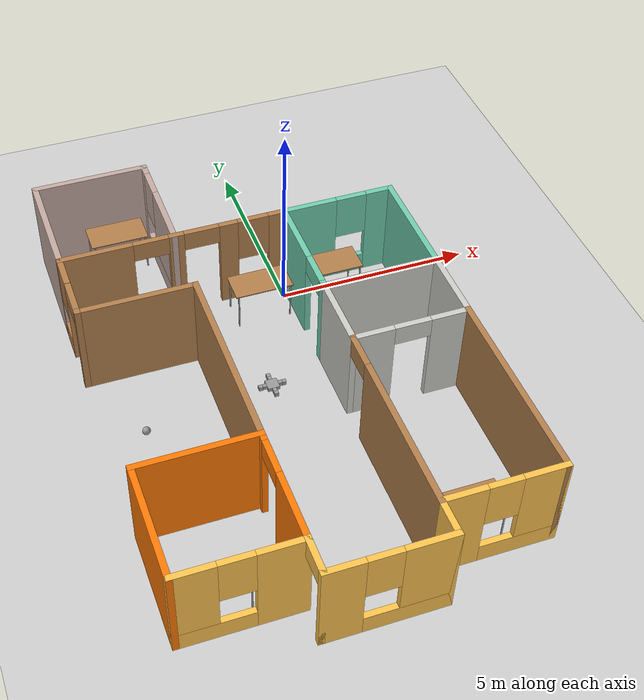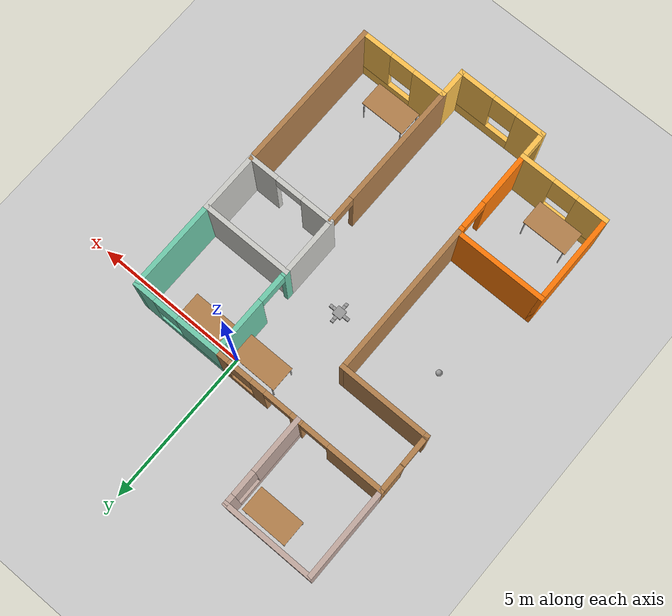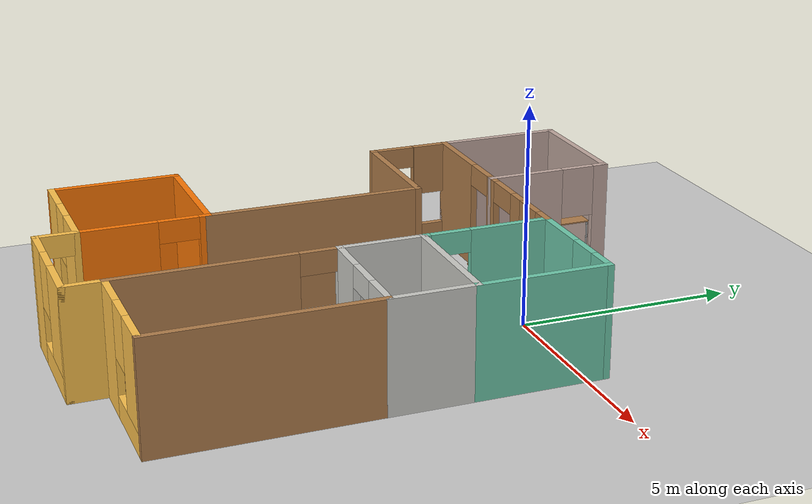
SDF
<sdf version="1.6">
 <world name="default">
  <plugin name="hello" filename="libhello.so"/>
  <light name="sun" type="directional">
   <pose>0 0 10 0 -0 0</pose>
   <diffuse>0.8 0.8 0.8 1</diffuse>
   <specular>0.2 0.2 0.2 1</specular>
   <attenuation>
    <range>1000</range>
    <constant>0.9</constant>
    <linear>0.01</linear>
    <quadratic>0.001</quadratic>
   </attenuation>
   <direction>-0.5 0.1 -0.9</direction>
  </light>
  <model name="ground_plane">
   <static>1</static>
   <link name="link">
    <collision name="collision">
     <geometry><plane><normal>0 0 1</normal><size>100 100</size></plane></geometry>
     <surface>
      <contact><collide_bitmask>65535</collide_bitmask></contact>
      <friction><ode><mu>100</mu><mu2>50</mu2></ode></friction>
     </surface>
    </collision>
    <visual name="visual">
     <cast_shadows>0</cast_shadows>
     <geometry><plane><normal>0 0 1</normal><size>100 100</size></plane></geometry>
     <material>
      <script><uri>file://media/materials/scripts/gazebo.material</uri><name>Gazebo/Grey</name></script>
     </material>
    </visual>
   </link>
  </model>
  <gravity>0 0 -9.8</gravity>
  <magnetic_field>6e-06 2.3e-05 -4.2e-05</magnetic_field>
  <atmosphere type="adiabatic"/>
  <physics name="default_physics" default="0" type="ode">
   <max_step_size>0.001</max_step_size>
   <real_time_factor>1</real_time_factor>
   <real_time_update_rate>1000</real_time_update_rate>
  </physics>
  <scene><ambient>0.4 0.4 0.4 1</ambient><background>0.7 0.7 0.7 1</background><shadows>1</shadows></scene>
  <spherical_coordinates>
   <surface_model>EARTH_WGS84</surface_model>
   <latitude_deg>0</latitude_deg>
   <longitude_deg>0</longitude_deg>
   <elevation>0</elevation>
   <heading_deg>0</heading_deg>
  </spherical_coordinates>
  <model name="myBuilding">
   <pose>-1.28727 -3.3563 0 0 -0 0</pose>
   <link name="Wall_1">
    <pose>0 -6.625 0 0 -0 0</pose>
    <visual name="Wall_1_Visual_0">
     <pose>-1.01471 0 1.25 0 -0 0</pose>
     <geometry><box><size>0.970584 0.15 2.5</size></box></geometry>
     <material>
      <script><uri>file://media/materials/scripts/gazebo.material</uri><name>Gazebo/Grey</name></script>
      <ambient>1 0.764706 0.305882 1</ambient>
     </material>
     <meta><layer>0</layer></meta>
    </visual>
    <collision name="Wall_1_Collision_0">
     <geometry><box><size>0.970584 0.15 2.5</size></box></geometry>
     <pose>-1.01471 0 1.25 0 -0 0</pose>
    </collision>
    <visual name="Wall_1_Visual_1">
     <pose>0.485292 0 0.25 0 -0 0</pose>
     <geometry><box><size>2.02942 0.15 0.5</size></box></geometry>
     <material>
      <script><uri>file://media/materials/scripts/gazebo.material</uri><name>Gazebo/Grey</name></script>
      <ambient>1 0.764706 0.305882 1</ambient>
     </material>
     <meta><layer>0</layer></meta>
    </visual>
    <collision name="Wall_1_Collision_1">
     <geometry><box><size>2.02942 0.15 0.5</size></box></geometry>
     <pose>0.485292 0 0.25 0 -0 0</pose>
    </collision>
    <visual name="Wall_1_Visual_2">
     <pose>0.885292 0 1.5 0 -0 0</pose>
     <geometry><box><size>1.22942 0.15 2</size></box></geometry>
     <material>
      <script><uri>file://media/materials/scripts/gazebo.material</uri><name>Gazebo/Grey</name></script>
      <ambient>1 0.764706 0.305882 1</ambient>
     </material>
     <meta><layer>0</layer></meta>
    </visual>
    <collision name="Wall_1_Collision_2">
     <geometry><box><size>1.22942 0.15 2</size></box></geometry>
     <pose>0.885292 0 1.5 0 -0 0</pose>
    </collision>
    <visual name="Wall_1_Visual_3">
     <pose>-0.129416 0 1.9 0 -0 0</pose>
     <geometry><box><size>0.8 0.15 1.2</size></box></geometry>
     <material>
      <script><uri>file://media/materials/scripts/gazebo.material</uri><name>Gazebo/Grey</name></script>
      <ambient>1 0.764706 0.305882 1</ambient>
     </material>
     <meta><layer>0</layer></meta>
    </visual>
    <collision name="Wall_1_Collision_3">
     <geometry><box><size>0.8 0.15 1.2</size></box></geometry>
     <pose>-0.129416 0 1.9 0 -0 0</pose>
    </collision>
   </link>
   <link name="Wall_10">
    <collision name="Wall_10_Collision">
     <geometry><box><size>3 0.15 2.5</size></box></geometry>
     <pose>0 0 1.25 0 -0 0</pose>
    </collision>
    <visual name="Wall_10_Visual">
     <pose>0 0 1.25 0 -0 0</pose>
     <geometry><box><size>3 0.15 2.5</size></box></geometry>
     <material>
      <script><uri>file://media/materials/scripts/gazebo.material</uri><name>Gazebo/CeilingTiled</name></script>
      <ambient>1 1 1 1</ambient>
     </material>
     <meta><layer>0</layer></meta>
    </visual>
    <pose>2.85 0.925 0 0 -0 3.14159</pose>
   </link>
   <link name="Wall_11">
    <collision name="Wall_11_Collision">
     <geometry><box><size>2 0.15 2.5</size></box></geometry>
     <pose>0 0 1.25 0 -0 0</pose>
    </collision>
    <visual name="Wall_11_Visual">
     <pose>0 0 1.25 0 -0 0</pose>
     <geometry><box><size>2 0.15 2.5</size></box></geometry>
     <material>
      <script><uri>file://media/materials/scripts/gazebo.material</uri><name>Gazebo/CeilingTiled</name></script>
      <ambient>1 1 1 1</ambient>
     </material>
     <meta><layer>0</layer></meta>
    </visual>
    <pose>1.425 0 0 0 0 -1.5708</pose>
   </link>
   <link name="Wall_13">
    <collision name="Wall_13_Collision">
     <geometry><box><size>3 0.15 2.5</size></box></geometry>
     <pose>0 0 1.25 0 -0 0</pose>
    </collision>
    <visual name="Wall_13_Visual">
     <pose>0 0 1.25 0 -0 0</pose>
     <geometry><box><size>3 0.15 2.5</size></box></geometry>
     <material>
      <script><uri>file://media/materials/scripts/gazebo.material</uri><name>Gazebo/Grey</name></script>
      <ambient>0.435294 0.796078 0.67451 1</ambient>
     </material>
     <meta><layer>0</layer></meta>
    </visual>
    <pose>4.275 2.35 0 0 -0 1.5708</pose>
   </link>
   <link name="Wall_14">
    <pose>2.85 3.775 0 0 -0 3.14159</pose>
    <visual name="Wall_14_Visual_0">
     <pose>-1.12972 0 1.25 0 -0 0</pose>
     <geometry><box><size>0.740563 0.15 2.5</size></box></geometry>
     <material>
      <script><uri>file://media/materials/scripts/gazebo.material</uri><name>Gazebo/Grey</name></script>
      <ambient>0.435294 0.796078 0.67451 1</ambient>
     </material>
     <meta><layer>0</layer></meta>
    </visual>
    <collision name="Wall_14_Collision_0">
     <geometry><box><size>0.740563 0.15 2.5</size></box></geometry>
     <pose>-1.12972 0 1.25 0 -0 0</pose>
    </collision>
    <visual name="Wall_14_Visual_1">
     <pose>0.370282 0 0.25 0 -0 0</pose>
     <geometry><box><size>2.25944 0.15 0.5</size></box></geometry>
     <material>
      <script><uri>file://media/materials/scripts/gazebo.material</uri><name>Gazebo/Grey</name></script>
      <ambient>0.435294 0.796078 0.67451 1</ambient>
     </material>
     <meta><layer>0</layer></meta>
    </visual>
    <collision name="Wall_14_Collision_1">
     <geometry><box><size>2.25944 0.15 0.5</size></box></geometry>
     <pose>0.370282 0 0.25 0 -0 0</pose>
    </collision>
    <visual name="Wall_14_Visual_2">
     <pose>0.770282 0 1.5 0 -0 0</pose>
     <geometry><box><size>1.45944 0.15 2</size></box></geometry>
     <material>
      <script><uri>file://media/materials/scripts/gazebo.material</uri><name>Gazebo/Grey</name></script>
      <ambient>0.435294 0.796078 0.67451 1</ambient>
     </material>
     <meta><layer>0</layer></meta>
    </visual>
    <collision name="Wall_14_Collision_2">
     <geometry><box><size>1.45944 0.15 2</size></box></geometry>
     <pose>0.770282 0 1.5 0 -0 0</pose>
    </collision>
    <visual name="Wall_14_Visual_3">
     <pose>-0.359437 0 1.9 0 -0 0</pose>
     <geometry><box><size>0.8 0.15 1.2</size></box></geometry>
     <material>
      <script><uri>file://media/materials/scripts/gazebo.material</uri><name>Gazebo/Grey</name></script>
      <ambient>0.435294 0.796078 0.67451 1</ambient>
     </material>
     <meta><layer>0</layer></meta>
    </visual>
    <collision name="Wall_14_Collision_3">
     <geometry><box><size>0.8 0.15 1.2</size></box></geometry>
     <pose>-0.359437 0 1.9 0 -0 0</pose>
    </collision>
   </link>
   <link name="Wall_15">
    <pose>1.425 2.35 0 0 0 -1.5708</pose>
    <visual name="Wall_15_Visual_0">
     <pose>-0.563237 0 1.25 0 -0 0</pose>
     <geometry><box><size>1.87353 0.15 2.5</size></box></geometry>
     <material>
      <script><uri>file://media/materials/scripts/gazebo.material</uri><name>Gazebo/Grey</name></script>
      <ambient>0.435294 0.796078 0.67451 1</ambient>
     </material>
     <meta><layer>0</layer></meta>
    </visual>
    <collision name="Wall_15_Collision_0">
     <geometry><box><size>1.87353 0.15 2.5</size></box></geometry>
     <pose>-0.563237 0 1.25 0 -0 0</pose>
    </collision>
    <visual name="Wall_15_Visual_1">
     <pose>1.38676 0 1.25 0 -0 0</pose>
     <geometry><box><size>0.226475 0.15 2.5</size></box></geometry>
     <material>
      <script><uri>file://media/materials/scripts/gazebo.material</uri><name>Gazebo/Grey</name></script>
      <ambient>0.435294 0.796078 0.67451 1</ambient>
     </material>
     <meta><layer>0</layer></meta>
    </visual>
    <collision name="Wall_15_Collision_1">
     <geometry><box><size>0.226475 0.15 2.5</size></box></geometry>
     <pose>1.38676 0 1.25 0 -0 0</pose>
    </collision>
    <visual name="Wall_15_Visual_2">
     <pose>0.823525 0 2.25 0 -0 0</pose>
     <geometry><box><size>0.9 0.15 0.5</size></box></geometry>
     <material>
      <script><uri>file://media/materials/scripts/gazebo.material</uri><name>Gazebo/Grey</name></script>
      <ambient>0.435294 0.796078 0.67451 1</ambient>
     </material>
     <meta><layer>0</layer></meta>
    </visual>
    <collision name="Wall_15_Collision_2">
     <geometry><box><size>0.9 0.15 0.5</size></box></geometry>
     <pose>0.823525 0 2.25 0 -0 0</pose>
    </collision>
   </link>
   <link name="Wall_17">
    <pose>-1.425 -6.2 0 0 -0 1.5708</pose>
    <visual name="Wall_17_Visual_0">
     <pose>-0.443398 0 1.25 0 -0 0</pose>
     <geometry><box><size>0.113204 0.15 2.5</size></box></geometry>
     <material>
      <script><uri>file://media/materials/scripts/gazebo.material</uri><name>Gazebo/Grey</name></script>
      <ambient>1 0.764706 0.305882 1</ambient>
     </material>
     <meta><layer>0</layer></meta>
    </visual>
    <collision name="Wall_17_Collision_0">
     <geometry><box><size>0.113204 0.15 2.5</size></box></geometry>
     <pose>-0.443398 0 1.25 0 -0 0</pose>
    </collision>
    <visual name="Wall_17_Visual_1">
     <pose>0.056602 0 2.25 0 -0 0</pose>
     <geometry><box><size>0.886796 0.15 0.5</size></box></geometry>
     <material>
      <script><uri>file://media/materials/scripts/gazebo.material</uri><name>Gazebo/Grey</name></script>
      <ambient>1 0.764706 0.305882 1</ambient>
     </material>
     <meta><layer>0</layer></meta>
    </visual>
    <collision name="Wall_17_Collision_1">
     <geometry><box><size>0.886796 0.15 0.5</size></box></geometry>
     <pose>0.056602 0 2.25 0 -0 0</pose>
    </collision>
   </link>
   <link name="Wall_18">
    <pose>-2.85 -5.775 0 0 -0 3.14159</pose>
    <visual name="Wall_18_Visual_0">
     <pose>-0.922456 0 1.25 0 -0 0</pose>
     <geometry><box><size>1.15509 0.15 2.5</size></box></geometry>
     <material>
      <script><uri>file://media/materials/scripts/gazebo.material</uri><name>Gazebo/Grey</name></script>
      <ambient>1 0.764706 0.305882 1</ambient>
     </material>
     <meta><layer>0</layer></meta>
    </visual>
    <collision name="Wall_18_Collision_0">
     <geometry><box><size>1.15509 0.15 2.5</size></box></geometry>
     <pose>-0.922456 0 1.25 0 -0 0</pose>
    </collision>
    <visual name="Wall_18_Visual_1">
     <pose>0.577544 0 0.25 0 -0 0</pose>
     <geometry><box><size>1.84491 0.15 0.5</size></box></geometry>
     <material>
      <script><uri>file://media/materials/scripts/gazebo.material</uri><name>Gazebo/Grey</name></script>
      <ambient>1 0.764706 0.305882 1</ambient>
     </material>
     <meta><layer>0</layer></meta>
    </visual>
    <collision name="Wall_18_Collision_1">
     <geometry><box><size>1.84491 0.15 0.5</size></box></geometry>
     <pose>0.577544 0 0.25 0 -0 0</pose>
    </collision>
    <visual name="Wall_18_Visual_2">
     <pose>0.977544 0 1.5 0 -0 0</pose>
     <geometry><box><size>1.04491 0.15 2</size></box></geometry>
     <material>
      <script><uri>file://media/materials/scripts/gazebo.material</uri><name>Gazebo/Grey</name></script>
      <ambient>1 0.764706 0.305882 1</ambient>
     </material>
     <meta><layer>0</layer></meta>
    </visual>
    <collision name="Wall_18_Collision_2">
     <geometry><box><size>1.04491 0.15 2</size></box></geometry>
     <pose>0.977544 0 1.5 0 -0 0</pose>
    </collision>
    <visual name="Wall_18_Visual_3">
     <pose>0.055089 0 1.9 0 -0 0</pose>
     <geometry><box><size>0.8 0.15 1.2</size></box></geometry>
     <material>
      <script><uri>file://media/materials/scripts/gazebo.material</uri><name>Gazebo/Grey</name></script>
      <ambient>1 0.764706 0.305882 1</ambient>
     </material>
     <meta><layer>0</layer></meta>
    </visual>
    <collision name="Wall_18_Collision_3">
     <geometry><box><size>0.8 0.15 1.2</size></box></geometry>
     <pose>0.055089 0 1.9 0 -0 0</pose>
    </collision>
   </link>
   <link name="Wall_19">
    <collision name="Wall_19_Collision">
     <geometry><box><size>3 0.15 2.5</size></box></geometry>
     <pose>0 0 1.25 0 -0 0</pose>
    </collision>
    <visual name="Wall_19_Visual">
     <pose>0 0 1.25 0 -0 0</pose>
     <geometry><box><size>3 0.15 2.5</size></box></geometry>
     <material>
      <script><uri>file://media/materials/scripts/gazebo.material</uri><name>Gazebo/Grey</name></script>
      <ambient>0.996078 0.47451 0.0196078 1</ambient>
     </material>
     <meta><layer>0</layer></meta>
    </visual>
    <pose>-4.275 -4.35 0 0 -0 1.5708</pose>
   </link>
   <link name="Wall_2">
    <collision name="Wall_2_Collision">
     <geometry><box><size>1 0.15 2.5</size></box></geometry>
     <pose>0 0 1.25 0 -0 0</pose>
    </collision>
    <visual name="Wall_2_Visual">
     <pose>0 0 1.25 0 -0 0</pose>
     <geometry><box><size>1 0.15 2.5</size></box></geometry>
     <material>
      <script><uri>file://media/materials/scripts/gazebo.material</uri><name>Gazebo/Grey</name></script>
      <ambient>1 0.764706 0.305882 1</ambient>
     </material>
     <meta><layer>0</layer></meta>
    </visual>
    <pose>1.425 -6.2 0 0 -0 1.5708</pose>
   </link>
   <link name="Wall_20">
    <collision name="Wall_20_Collision">
     <geometry><box><size>3 0.15 2.5</size></box></geometry>
     <pose>0 0 1.25 0 -0 0</pose>
    </collision>
    <visual name="Wall_20_Visual">
     <pose>0 0 1.25 0 -0 0</pose>
     <geometry><box><size>3 0.15 2.5</size></box></geometry>
     <material>
      <script><uri>file://media/materials/scripts/gazebo.material</uri><name>Gazebo/Grey</name></script>
      <ambient>0.996078 0.47451 0.0196078 1</ambient>
     </material>
     <meta><layer>0</layer></meta>
    </visual>
    <pose>-2.85 -2.925 0 0 -0 0</pose>
   </link>
   <link name="Wall_21">
    <pose>-1.425 -4.35 0 0 0 -1.5708</pose>
    <visual name="Wall_21_Visual_0">
     <pose>-1.35881 0 1.25 0 -0 0</pose>
     <geometry><box><size>0.282373 0.15 2.5</size></box></geometry>
     <material>
      <script><uri>file://media/materials/scripts/gazebo.material</uri><name>Gazebo/Grey</name></script>
      <ambient>0.996078 0.47451 0.0196078 1</ambient>
     </material>
     <meta><layer>0</layer></meta>
    </visual>
    <collision name="Wall_21_Collision_0">
     <geometry><box><size>0.282373 0.15 2.5</size></box></geometry>
     <pose>-1.35881 0 1.25 0 -0 0</pose>
    </collision>
    <visual name="Wall_21_Visual_1">
     <pose>0.591186 0 1.25 0 -0 0</pose>
     <geometry><box><size>1.81763 0.15 2.5</size></box></geometry>
     <material>
      <script><uri>file://media/materials/scripts/gazebo.material</uri><name>Gazebo/Grey</name></script>
      <ambient>0.996078 0.47451 0.0196078 1</ambient>
     </material>
     <meta><layer>0</layer></meta>
    </visual>
    <collision name="Wall_21_Collision_1">
     <geometry><box><size>1.81763 0.15 2.5</size></box></geometry>
     <pose>0.591186 0 1.25 0 -0 0</pose>
    </collision>
    <visual name="Wall_21_Visual_2">
     <pose>-0.767627 0 2.25 0 -0 0</pose>
     <geometry><box><size>0.9 0.15 0.5</size></box></geometry>
     <material>
      <script><uri>file://media/materials/scripts/gazebo.material</uri><name>Gazebo/Grey</name></script>
      <ambient>0.996078 0.47451 0.0196078 1</ambient>
     </material>
     <meta><layer>0</layer></meta>
    </visual>
    <collision name="Wall_21_Collision_2">
     <geometry><box><size>0.9 0.15 0.5</size></box></geometry>
     <pose>-0.767627 0 2.25 0 -0 0</pose>
    </collision>
   </link>
   <link name="Wall_24">
    <collision name="Wall_24_Collision">
     <geometry><box><size>5 0.15 2.5</size></box></geometry>
     <pose>0 0 1.25 0 -0 0</pose>
    </collision>
    <visual name="Wall_24_Visual">
     <pose>0 0 1.25 0 -0 0</pose>
     <geometry><box><size>5 0.15 2.5</size></box></geometry>
     <material>
      <script><uri>file://media/materials/scripts/gazebo.material</uri><name>Gazebo/Wood</name></script>
      <ambient>1 1 1 1</ambient>
     </material>
     <meta><layer>0</layer></meta>
    </visual>
    <pose>-1.425 -0.5 0 0 -0 1.5708</pose>
   </link>
   <link name="Wall_25">
    <collision name="Wall_25_Collision">
     <geometry><box><size>3 0.15 2.5</size></box></geometry>
     <pose>0 0 1.25 0 -0 0</pose>
    </collision>
    <visual name="Wall_25_Visual">
     <pose>0 0 1.25 0 -0 0</pose>
     <geometry><box><size>3 0.15 2.5</size></box></geometry>
     <material>
      <script><uri>file://media/materials/scripts/gazebo.material</uri><name>Gazebo/Wood</name></script>
      <ambient>1 1 1 1</ambient>
     </material>
     <meta><layer>0</layer></meta>
    </visual>
    <pose>-2.85 1.925 0 0 -0 3.14159</pose>
   </link>
   <link name="Wall_3">
    <pose>2.85 -5.775 0 0 -0 0</pose>
    <visual name="Wall_3_Visual_0">
     <pose>-0.941247 0 1.25 0 -0 0</pose>
     <geometry><box><size>1.11751 0.15 2.5</size></box></geometry>
     <material>
      <script><uri>file://media/materials/scripts/gazebo.material</uri><name>Gazebo/Grey</name></script>
      <ambient>1 0.764706 0.305882 1</ambient>
     </material>
     <meta><layer>0</layer></meta>
    </visual>
    <collision name="Wall_3_Collision_0">
     <geometry><box><size>1.11751 0.15 2.5</size></box></geometry>
     <pose>-0.941247 0 1.25 0 -0 0</pose>
    </collision>
    <visual name="Wall_3_Visual_1">
     <pose>0.558753 0 0.25 0 -0 0</pose>
     <geometry><box><size>1.88249 0.15 0.5</size></box></geometry>
     <material>
      <script><uri>file://media/materials/scripts/gazebo.material</uri><name>Gazebo/Grey</name></script>
      <ambient>1 0.764706 0.305882 1</ambient>
     </material>
     <meta><layer>0</layer></meta>
    </visual>
    <collision name="Wall_3_Collision_1">
     <geometry><box><size>1.88249 0.15 0.5</size></box></geometry>
     <pose>0.558753 0 0.25 0 -0 0</pose>
    </collision>
    <visual name="Wall_3_Visual_2">
     <pose>0.958753 0 1.5 0 -0 0</pose>
     <geometry><box><size>1.08249 0.15 2</size></box></geometry>
     <material>
      <script><uri>file://media/materials/scripts/gazebo.material</uri><name>Gazebo/Grey</name></script>
      <ambient>1 0.764706 0.305882 1</ambient>
     </material>
     <meta><layer>0</layer></meta>
    </visual>
    <collision name="Wall_3_Collision_2">
     <geometry><box><size>1.08249 0.15 2</size></box></geometry>
     <pose>0.958753 0 1.5 0 -0 0</pose>
    </collision>
    <visual name="Wall_3_Visual_3">
     <pose>0.017506 0 1.9 0 -0 0</pose>
     <geometry><box><size>0.8 0.15 1.2</size></box></geometry>
     <material>
      <script><uri>file://media/materials/scripts/gazebo.material</uri><name>Gazebo/Grey</name></script>
      <ambient>1 0.764706 0.305882 1</ambient>
     </material>
     <meta><layer>0</layer></meta>
    </visual>
    <collision name="Wall_3_Collision_3">
     <geometry><box><size>0.8 0.15 1.2</size></box></geometry>
     <pose>0.017506 0 1.9 0 -0 0</pose>
    </collision>
   </link>
   <link name="Wall_30">
    <pose>-4.275 2.85 0 0 -0 1.5708</pose>
    <visual name="Wall_30_Visual_0">
     <pose>-0.914094 0 1.25 0 -0 0</pose>
     <geometry><box><size>0.171813 0.15 2.5</size></box></geometry>
     <material>
      <script><uri>file://media/materials/scripts/gazebo.material</uri><name>Gazebo/Wood</name></script>
      <ambient>1 1 1 1</ambient>
     </material>
     <meta><layer>0</layer></meta>
    </visual>
    <collision name="Wall_30_Collision_0">
     <geometry><box><size>0.171813 0.15 2.5</size></box></geometry>
     <pose>-0.914094 0 1.25 0 -0 0</pose>
    </collision>
    <visual name="Wall_30_Visual_1">
     <pose>0.079254 0 1.25 0 -0 0</pose>
     <geometry><box><size>0.014884 0.15 2.5</size></box></geometry>
     <material>
      <script><uri>file://media/materials/scripts/gazebo.material</uri><name>Gazebo/Wood</name></script>
      <ambient>1 1 1 1</ambient>
     </material>
     <meta><layer>0</layer></meta>
    </visual>
    <collision name="Wall_30_Collision_1">
     <geometry><box><size>0.014884 0.15 2.5</size></box></geometry>
     <pose>0.079254 0 1.25 0 -0 0</pose>
    </collision>
    <visual name="Wall_30_Visual_2">
     <pose>0.543348 0 0.25 0 -0 0</pose>
     <geometry><box><size>0.913304 0.15 0.5</size></box></geometry>
     <material>
      <script><uri>file://media/materials/scripts/gazebo.material</uri><name>Gazebo/Wood</name></script>
      <ambient>1 1 1 1</ambient>
     </material>
     <meta><layer>0</layer></meta>
    </visual>
    <collision name="Wall_30_Collision_2">
     <geometry><box><size>0.913304 0.15 0.5</size></box></geometry>
     <pose>0.543348 0 0.25 0 -0 0</pose>
    </collision>
    <visual name="Wall_30_Visual_3">
     <pose>0.943348 0 1.5 0 -0 0</pose>
     <geometry><box><size>0.113304 0.15 2</size></box></geometry>
     <material>
      <script><uri>file://media/materials/scripts/gazebo.material</uri><name>Gazebo/Wood</name></script>
      <ambient>1 1 1 1</ambient>
     </material>
     <meta><layer>0</layer></meta>
    </visual>
    <collision name="Wall_30_Collision_3">
     <geometry><box><size>0.113304 0.15 2</size></box></geometry>
     <pose>0.943348 0 1.5 0 -0 0</pose>
    </collision>
    <visual name="Wall_30_Visual_4">
     <pose>0.486696 0 1.9 0 -0 0</pose>
     <geometry><box><size>0.8 0.15 1.2</size></box></geometry>
     <material>
      <script><uri>file://media/materials/scripts/gazebo.material</uri><name>Gazebo/Wood</name></script>
      <ambient>1 1 1 1</ambient>
     </material>
     <meta><layer>0</layer></meta>
    </visual>
    <collision name="Wall_30_Collision_4">
     <geometry><box><size>0.8 0.15 1.2</size></box></geometry>
     <pose>0.486696 0 1.9 0 -0 0</pose>
    </collision>
    <visual name="Wall_30_Visual_5">
     <pose>-0.378187 0 2.25 0 -0 0</pose>
     <geometry><box><size>0.9 0.15 0.5</size></box></geometry>
     <material>
      <script><uri>file://media/materials/scripts/gazebo.material</uri><name>Gazebo/Wood</name></script>
      <ambient>1 1 1 1</ambient>
     </material>
     <meta><layer>0</layer></meta>
    </visual>
    <collision name="Wall_30_Collision_5">
     <geometry><box><size>0.9 0.15 0.5</size></box></geometry>
     <pose>-0.378187 0 2.25 0 -0 0</pose>
    </collision>
   </link>
   <link name="Wall_31">
    <pose>-1.425 3.775 0 0 -0 0</pose>
    <visual name="Wall_31_Visual_0">
     <pose>-1.98505 0 1.25 0 -0 0</pose>
     <geometry><box><size>1.87991 0.15 2.5</size></box></geometry>
     <material>
      <script><uri>file://media/materials/scripts/gazebo.material</uri><name>Gazebo/Wood</name></script>
      <ambient>1 1 1 1</ambient>
     </material>
     <meta><layer>0</layer></meta>
    </visual>
    <collision name="Wall_31_Collision_0">
     <geometry><box><size>1.87991 0.15 2.5</size></box></geometry>
     <pose>-1.98505 0 1.25 0 -0 0</pose>
    </collision>
    <visual name="Wall_31_Visual_1">
     <pose>0.048542 0 1.25 0 -0 0</pose>
     <geometry><box><size>0.387269 0.15 2.5</size></box></geometry>
     <material>
      <script><uri>file://media/materials/scripts/gazebo.material</uri><name>Gazebo/Wood</name></script>
      <ambient>1 1 1 1</ambient>
     </material>
     <meta><layer>0</layer></meta>
    </visual>
    <collision name="Wall_31_Collision_1">
     <geometry><box><size>0.387269 0.15 2.5</size></box></geometry>
     <pose>0.048542 0 1.25 0 -0 0</pose>
    </collision>
    <visual name="Wall_31_Visual_2">
     <pose>1.38092 0 1.25 0 -0 0</pose>
     <geometry><box><size>0.477496 0.15 2.5</size></box></geometry>
     <material>
      <script><uri>file://media/materials/scripts/gazebo.material</uri><name>Gazebo/Wood</name></script>
      <ambient>1 1 1 1</ambient>
     </material>
     <meta><layer>0</layer></meta>
    </visual>
    <collision name="Wall_31_Collision_2">
     <geometry><box><size>0.477496 0.15 2.5</size></box></geometry>
     <pose>1.38092 0 1.25 0 -0 0</pose>
    </collision>
    <visual name="Wall_31_Visual_3">
     <pose>2.27234 0 0.25 0 -0 0</pose>
     <geometry><box><size>1.30533 0.15 0.5</size></box></geometry>
     <material>
      <script><uri>file://media/materials/scripts/gazebo.material</uri><name>Gazebo/Wood</name></script>
      <ambient>1 1 1 1</ambient>
     </material>
     <meta><layer>0</layer></meta>
    </visual>
    <collision name="Wall_31_Collision_3">
     <geometry><box><size>1.30533 0.15 0.5</size></box></geometry>
     <pose>2.27234 0 0.25 0 -0 0</pose>
    </collision>
    <visual name="Wall_31_Visual_4">
     <pose>2.67234 0 1.5 0 -0 0</pose>
     <geometry><box><size>0.505327 0.15 2</size></box></geometry>
     <material>
      <script><uri>file://media/materials/scripts/gazebo.material</uri><name>Gazebo/Wood</name></script>
      <ambient>1 1 1 1</ambient>
     </material>
     <meta><layer>0</layer></meta>
    </visual>
    <collision name="Wall_31_Collision_4">
     <geometry><box><size>0.505327 0.15 2</size></box></geometry>
     <pose>2.67234 0 1.5 0 -0 0</pose>
    </collision>
    <visual name="Wall_31_Visual_5">
     <pose>2.01967 0 1.9 0 -0 0</pose>
     <geometry><box><size>0.8 0.15 1.2</size></box></geometry>
     <material>
      <script><uri>file://media/materials/scripts/gazebo.material</uri><name>Gazebo/Wood</name></script>
      <ambient>1 1 1 1</ambient>
     </material>
     <meta><layer>0</layer></meta>
    </visual>
    <collision name="Wall_31_Collision_5">
     <geometry><box><size>0.8 0.15 1.2</size></box></geometry>
     <pose>2.01967 0 1.9 0 -0 0</pose>
    </collision>
    <visual name="Wall_31_Visual_6">
     <pose>-0.595092 0 2.25 0 -0 0</pose>
     <geometry><box><size>0.9 0.15 0.5</size></box></geometry>
     <material>
      <script><uri>file://media/materials/scripts/gazebo.material</uri><name>Gazebo/Wood</name></script>
      <ambient>1 1 1 1</ambient>
     </material>
     <meta><layer>0</layer></meta>
    </visual>
    <collision name="Wall_31_Collision_6">
     <geometry><box><size>0.9 0.15 0.5</size></box></geometry>
     <pose>-0.595092 0 2.25 0 -0 0</pose>
    </collision>
    <visual name="Wall_31_Visual_7">
     <pose>0.692177 0 2.25 0 -0 0</pose>
     <geometry><box><size>0.9 0.15 0.5</size></box></geometry>
     <material>
      <script><uri>file://media/materials/scripts/gazebo.material</uri><name>Gazebo/Wood</name></script>
      <ambient>1 1 1 1</ambient>
     </material>
     <meta><layer>0</layer></meta>
    </visual>
    <collision name="Wall_31_Collision_7">
     <geometry><box><size>0.9 0.15 0.5</size></box></geometry>
     <pose>0.692177 0 2.25 0 -0 0</pose>
    </collision>
   </link>
   <link name="Wall_33">
    <collision name="Wall_33_Collision">
     <geometry><box><size>3 0.15 2.5</size></box></geometry>
     <pose>0 0 1.25 0 -0 0</pose>
    </collision>
    <visual name="Wall_33_Visual">
     <pose>0 0 1.25 0 -0 0</pose>
     <geometry><box><size>3 0.15 2.5</size></box></geometry>
     <material>
      <script><uri>file://media/materials/scripts/gazebo.material</uri><name>Gazebo/Grey</name></script>
      <ambient>0.760784 0.662745 0.627451 1</ambient>
     </material>
     <meta><layer>0</layer></meta>
    </visual>
    <pose>-4.275 5.2 0 0 -0 1.5708</pose>
   </link>
   <link name="Wall_34">
    <collision name="Wall_34_Collision">
     <geometry><box><size>3 0.15 2.5</size></box></geometry>
     <pose>0 0 1.25 0 -0 0</pose>
    </collision>
    <visual name="Wall_34_Visual">
     <pose>0 0 1.25 0 -0 0</pose>
     <geometry><box><size>3 0.15 2.5</size></box></geometry>
     <material>
      <script><uri>file://media/materials/scripts/gazebo.material</uri><name>Gazebo/Grey</name></script>
      <ambient>0.760784 0.662745 0.627451 1</ambient>
     </material>
     <meta><layer>0</layer></meta>
    </visual>
    <pose>-2.85 6.625 0 0 -0 0</pose>
   </link>
   <link name="Wall_35">
    <pose>-1.425 5.2 0 0 0 -1.5708</pose>
    <visual name="Wall_35_Visual_0">
     <pose>-1.31567 0 1.25 0 -0 0</pose>
     <geometry><box><size>0.368653 0.15 2.5</size></box></geometry>
     <material>
      <script><uri>file://media/materials/scripts/gazebo.material</uri><name>Gazebo/Grey</name></script>
      <ambient>0.760784 0.662745 0.627451 1</ambient>
     </material>
     <meta><layer>0</layer></meta>
    </visual>
    <collision name="Wall_35_Collision_0">
     <geometry><box><size>0.368653 0.15 2.5</size></box></geometry>
     <pose>-1.31567 0 1.25 0 -0 0</pose>
    </collision>
    <visual name="Wall_35_Visual_1">
     <pose>0.184327 0 0.25 0 -0 0</pose>
     <geometry><box><size>2.63135 0.15 0.5</size></box></geometry>
     <material>
      <script><uri>file://media/materials/scripts/gazebo.material</uri><name>Gazebo/Grey</name></script>
      <ambient>0.760784 0.662745 0.627451 1</ambient>
     </material>
     <meta><layer>0</layer></meta>
    </visual>
    <collision name="Wall_35_Collision_1">
     <geometry><box><size>2.63135 0.15 0.5</size></box></geometry>
     <pose>0.184327 0 0.25 0 -0 0</pose>
    </collision>
    <visual name="Wall_35_Visual_2">
     <pose>0.584327 0 1.5 0 -0 0</pose>
     <geometry><box><size>1.83135 0.15 2</size></box></geometry>
     <material>
      <script><uri>file://media/materials/scripts/gazebo.material</uri><name>Gazebo/Grey</name></script>
      <ambient>0.760784 0.662745 0.627451 1</ambient>
     </material>
     <meta><layer>0</layer></meta>
    </visual>
    <collision name="Wall_35_Collision_2">
     <geometry><box><size>1.83135 0.15 2</size></box></geometry>
     <pose>0.584327 0 1.5 0 -0 0</pose>
    </collision>
    <visual name="Wall_35_Visual_3">
     <pose>-0.731347 0 1.9 0 -0 0</pose>
     <geometry><box><size>0.8 0.15 1.2</size></box></geometry>
     <material>
      <script><uri>file://media/materials/scripts/gazebo.material</uri><name>Gazebo/Grey</name></script>
      <ambient>0.760784 0.662745 0.627451 1</ambient>
     </material>
     <meta><layer>0</layer></meta>
    </visual>
    <collision name="Wall_35_Collision_3">
     <geometry><box><size>0.8 0.15 1.2</size></box></geometry>
     <pose>-0.731347 0 1.9 0 -0 0</pose>
    </collision>
   </link>
   <link name="Wall_5">
    <collision name="Wall_5_Collision">
     <geometry><box><size>5 0.15 2.5</size></box></geometry>
     <pose>0 0 1.25 0 -0 0</pose>
    </collision>
    <visual name="Wall_5_Visual">
     <pose>0 0 1.25 0 -0 0</pose>
     <geometry><box><size>5 0.15 2.5</size></box></geometry>
     <material>
      <script><uri>file://media/materials/scripts/gazebo.material</uri><name>Gazebo/Wood</name></script>
      <ambient>1 1 1 1</ambient>
     </material>
     <meta><layer>0</layer></meta>
    </visual>
    <pose>4.275 -3.35 0 0 -0 1.5708</pose>
   </link>
   <link name="Wall_6">
    <pose>2.85 -0.925 0 0 -0 3.14159</pose>
    <visual name="Wall_6_Visual_0">
     <pose>-0.99381 0 1.25 0 -0 0</pose>
     <geometry><box><size>1.01238 0.15 2.5</size></box></geometry>
     <material>
      <script><uri>file://media/materials/scripts/gazebo.material</uri><name>Gazebo/CeilingTiled</name></script>
      <ambient>1 1 1 1</ambient>
     </material>
     <meta><layer>0</layer></meta>
    </visual>
    <collision name="Wall_6_Collision_0">
     <geometry><box><size>1.01238 0.15 2.5</size></box></geometry>
     <pose>-0.99381 0 1.25 0 -0 0</pose>
    </collision>
    <visual name="Wall_6_Visual_1">
     <pose>0.95619 0 1.25 0 -0 0</pose>
     <geometry><box><size>1.08762 0.15 2.5</size></box></geometry>
     <material>
      <script><uri>file://media/materials/scripts/gazebo.material</uri><name>Gazebo/CeilingTiled</name></script>
      <ambient>1 1 1 1</ambient>
     </material>
     <meta><layer>0</layer></meta>
    </visual>
    <collision name="Wall_6_Collision_1">
     <geometry><box><size>1.08762 0.15 2.5</size></box></geometry>
     <pose>0.95619 0 1.25 0 -0 0</pose>
    </collision>
    <visual name="Wall_6_Visual_2">
     <pose>-0.03762 0 2.25 0 -0 0</pose>
     <geometry><box><size>0.9 0.15 0.5</size></box></geometry>
     <material>
      <script><uri>file://media/materials/scripts/gazebo.material</uri><name>Gazebo/CeilingTiled</name></script>
      <ambient>1 1 1 1</ambient>
     </material>
     <meta><layer>0</layer></meta>
    </visual>
    <collision name="Wall_6_Collision_2">
     <geometry><box><size>0.9 0.15 0.5</size></box></geometry>
     <pose>-0.03762 0 2.25 0 -0 0</pose>
    </collision>
   </link>
   <link name="Wall_7">
    <pose>1.425 -3.35 0 0 0 -1.5708</pose>
    <visual name="Wall_7_Visual_0">
     <pose>-2.47512 0 1.25 0 -0 0</pose>
     <geometry><box><size>0.049766 0.15 2.5</size></box></geometry>
     <material>
      <script><uri>file://media/materials/scripts/gazebo.material</uri><name>Gazebo/Wood</name></script>
      <ambient>1 1 1 1</ambient>
     </material>
     <meta><layer>0</layer></meta>
    </visual>
    <collision name="Wall_7_Collision_0">
     <geometry><box><size>0.049766 0.15 2.5</size></box></geometry>
     <pose>-2.47512 0 1.25 0 -0 0</pose>
    </collision>
    <visual name="Wall_7_Visual_1">
     <pose>0.474883 0 1.25 0 -0 0</pose>
     <geometry><box><size>4.05023 0.15 2.5</size></box></geometry>
     <material>
      <script><uri>file://media/materials/scripts/gazebo.material</uri><name>Gazebo/Wood</name></script>
      <ambient>1 1 1 1</ambient>
     </material>
     <meta><layer>0</layer></meta>
    </visual>
    <collision name="Wall_7_Collision_1">
     <geometry><box><size>4.05023 0.15 2.5</size></box></geometry>
     <pose>0.474883 0 1.25 0 -0 0</pose>
    </collision>
    <visual name="Wall_7_Visual_2">
     <pose>-2.00023 0 2.25 0 -0 0</pose>
     <geometry><box><size>0.9 0.15 0.5</size></box></geometry>
     <material>
      <script><uri>file://media/materials/scripts/gazebo.material</uri><name>Gazebo/Wood</name></script>
      <ambient>1 1 1 1</ambient>
     </material>
     <meta><layer>0</layer></meta>
    </visual>
    <collision name="Wall_7_Collision_2">
     <geometry><box><size>0.9 0.15 0.5</size></box></geometry>
     <pose>-2.00023 0 2.25 0 -0 0</pose>
    </collision>
   </link>
   <link name="Wall_9">
    <collision name="Wall_9_Collision">
     <geometry><box><size>2 0.15 2.5</size></box></geometry>
     <pose>0 0 1.25 0 -0 0</pose>
    </collision>
    <visual name="Wall_9_Visual">
     <pose>0 0 1.25 0 -0 0</pose>
     <geometry><box><size>2 0.15 2.5</size></box></geometry>
     <material>
      <script><uri>file://media/materials/scripts/gazebo.material</uri><name>Gazebo/CeilingTiled</name></script>
      <ambient>1 1 1 1</ambient>
     </material>
     <meta><layer>0</layer></meta>
    </visual>
    <pose>4.275 0 0 0 -0 1.5708</pose>
   </link>
   <static>1</static>
  </model>
  <model name="myLegged">
   <link name="link_0">
    <pose>0 0 0.044444 0 -0 0</pose>
    <inertial>
     <mass>1</mass>
     <inertia>
      <ixx>0.166667</ixx>
      <ixy>0</ixy>
      <ixz>0</ixz>
      <iyy>0.166667</iyy>
      <iyz>0</iyz>
      <izz>0.166667</izz>
     </inertia>
    </inertial>
    <visual name="visual">
     <geometry><box><size>0.3 0.3 0.1</size></box></geometry>
     <material>
      <lighting>1</lighting>
      <script><uri>file://media/materials/scripts/gazebo.material</uri><name>Gazebo/Grey</name></script>
      <shader type="pixel"><normal_map>__default__</normal_map></shader>
      <ambient>0.3 0.3 0.3 1</ambient>
      <diffuse>0.7 0.7 0.7 1</diffuse>
      <specular>0.01 0.01 0.01 1</specular>
      <emissive>0 0 0 1</emissive>
     </material>
    </visual>
    <collision name="collision">
     <geometry><box><size>0.3 0.3 0.1</size></box></geometry>
     <surface>
      <friction>
       <ode><mu>1</mu><mu2>1</mu2><fdir1>0 0 0</fdir1><slip1>0</slip1><slip2>0</slip2></ode>
       <torsional>
        <coefficient>1</coefficient>
        <patch_radius>0</patch_radius>
        <surface_radius>0</surface_radius>
        <use_patch_radius>1</use_patch_radius>
        <ode><slip>0</slip></ode>
       </torsional>
      </friction>
      <bounce><restitution_coefficient>0</restitution_coefficient><threshold>1e+06</threshold></bounce>
      <contact>
       <collide_without_contact>0</collide_without_contact>
       <collide_without_contact_bitmask>1</collide_without_contact_bitmask>
       <collide_bitmask>1</collide_bitmask>
       <ode>
        <soft_cfm>0</soft_cfm>
        <soft_erp>0.2</soft_erp>
        <kp>1e+13</kp>
        <kd>1</kd>
        <max_vel>0.01</max_vel>
        <min_depth>0</min_depth>
       </ode>
       <bullet>
        <split_impulse>1</split_impulse>
        <split_impulse_penetration_threshold>-0.01</split_impulse_penetration_threshold>
        <soft_cfm>0</soft_cfm>
        <soft_erp>0.2</soft_erp>
        <kp>1e+13</kp>
        <kd>1</kd>
       </bullet>
      </contact>
     </surface>
    </collision>
   </link>
   <link name="link_1">
    <pose>0 -0.2 0.044444 0 -0 0</pose>
    <inertial>
     <mass>1</mass>
     <inertia>
      <ixx>0.166667</ixx>
      <ixy>0</ixy>
      <ixz>0</ixz>
      <iyy>0.166667</iyy>
      <iyz>0</iyz>
      <izz>0.166667</izz>
     </inertia>
    </inertial>
    <visual name="visual">
     <geometry><box><size>0.1 0.1 0.1</size></box></geometry>
     <material>
      <lighting>1</lighting>
      <script><uri>file://media/materials/scripts/gazebo.material</uri><name>Gazebo/Grey</name></script>
      <shader type="pixel"><normal_map>__default__</normal_map></shader>
      <ambient>0.3 0.3 0.3 1</ambient>
      <diffuse>0.7 0.7 0.7 1</diffuse>
      <specular>0.01 0.01 0.01 1</specular>
      <emissive>0 0 0 1</emissive>
     </material>
    </visual>
    <collision name="collision">
     <geometry><box><size>0.1 0.1 0.1</size></box></geometry>
     <surface>
      <friction>
       <ode><mu>1</mu><mu2>1</mu2><fdir1>0 0 0</fdir1><slip1>0</slip1><slip2>0</slip2></ode>
       <torsional>
        <coefficient>1</coefficient>
        <patch_radius>0</patch_radius>
        <surface_radius>0</surface_radius>
        <use_patch_radius>1</use_patch_radius>
        <ode><slip>0</slip></ode>
       </torsional>
      </friction>
      <bounce><restitution_coefficient>0</restitution_coefficient><threshold>1e+06</threshold></bounce>
      <contact>
       <collide_without_contact>0</collide_without_contact>
       <collide_without_contact_bitmask>1</collide_without_contact_bitmask>
       <collide_bitmask>1</collide_bitmask>
       <ode>
        <soft_cfm>0</soft_cfm>
        <soft_erp>0.2</soft_erp>
        <kp>1e+13</kp>
        <kd>1</kd>
        <max_vel>0.01</max_vel>
        <min_depth>0</min_depth>
       </ode>
       <bullet>
        <split_impulse>1</split_impulse>
        <split_impulse_penetration_threshold>-0.01</split_impulse_penetration_threshold>
        <soft_cfm>0</soft_cfm>
        <soft_erp>0.2</soft_erp>
        <kp>1e+13</kp>
        <kd>1</kd>
       </bullet>
      </contact>
     </surface>
    </collision>
   </link>
   <link name="link_1_clone">
    <pose>-0.2 0 0.044444 0 -0 0</pose>
    <inertial>
     <mass>1</mass>
     <inertia>
      <ixx>0.166667</ixx>
      <ixy>0</ixy>
      <ixz>0</ixz>
      <iyy>0.166667</iyy>
      <iyz>0</iyz>
      <izz>0.166667</izz>
     </inertia>
    </inertial>
    <visual name="visual">
     <geometry><box><size>0.1 0.1 0.1</size></box></geometry>
     <material>
      <lighting>1</lighting>
      <script><uri>file://media/materials/scripts/gazebo.material</uri><name>Gazebo/Grey</name></script>
      <shader type="pixel"><normal_map>__default__</normal_map></shader>
      <ambient>0.3 0.3 0.3 1</ambient>
      <diffuse>0.7 0.7 0.7 1</diffuse>
      <specular>0.01 0.01 0.01 1</specular>
      <emissive>0 0 0 1</emissive>
     </material>
    </visual>
    <collision name="collision">
     <geometry><box><size>0.1 0.1 0.1</size></box></geometry>
     <surface>
      <friction>
       <ode><mu>1</mu><mu2>1</mu2><fdir1>0 0 0</fdir1><slip1>0</slip1><slip2>0</slip2></ode>
       <torsional>
        <coefficient>1</coefficient>
        <patch_radius>0</patch_radius>
        <surface_radius>0</surface_radius>
        <use_patch_radius>1</use_patch_radius>
        <ode><slip>0</slip></ode>
       </torsional>
      </friction>
      <bounce><restitution_coefficient>0</restitution_coefficient><threshold>1e+06</threshold></bounce>
      <contact>
       <collide_without_contact>0</collide_without_contact>
       <collide_without_contact_bitmask>1</collide_without_contact_bitmask>
       <collide_bitmask>1</collide_bitmask>
       <ode>
        <soft_cfm>0</soft_cfm>
        <soft_erp>0.2</soft_erp>
        <kp>1e+13</kp>
        <kd>1</kd>
        <max_vel>0.01</max_vel>
        <min_depth>0</min_depth>
       </ode>
       <bullet>
        <split_impulse>1</split_impulse>
        <split_impulse_penetration_threshold>-0.01</split_impulse_penetration_threshold>
        <soft_cfm>0</soft_cfm>
        <soft_erp>0.2</soft_erp>
        <kp>1e+13</kp>
        <kd>1</kd>
       </bullet>
      </contact>
     </surface>
    </collision>
   </link>
   <link name="link_1_clone_0">
    <pose>0.2 0 0.044444 0 -0 0</pose>
    <inertial>
     <mass>1</mass>
     <inertia>
      <ixx>0.166667</ixx>
      <ixy>0</ixy>
      <ixz>0</ixz>
      <iyy>0.166667</iyy>
      <iyz>0</iyz>
      <izz>0.166667</izz>
     </inertia>
    </inertial>
    <visual name="visual">
     <geometry><box><size>0.1 0.1 0.1</size></box></geometry>
     <material>
      <lighting>1</lighting>
      <script><uri>file://media/materials/scripts/gazebo.material</uri><name>Gazebo/Grey</name></script>
      <shader type="pixel"><normal_map>__default__</normal_map></shader>
      <ambient>0.3 0.3 0.3 1</ambient>
      <diffuse>0.7 0.7 0.7 1</diffuse>
      <specular>0.01 0.01 0.01 1</specular>
      <emissive>0 0 0 1</emissive>
     </material>
    </visual>
    <collision name="collision">
     <geometry><box><size>0.1 0.1 0.1</size></box></geometry>
     <surface>
      <friction>
       <ode><mu>1</mu><mu2>1</mu2><fdir1>0 0 0</fdir1><slip1>0</slip1><slip2>0</slip2></ode>
       <torsional>
        <coefficient>1</coefficient>
        <patch_radius>0</patch_radius>
        <surface_radius>0</surface_radius>
        <use_patch_radius>1</use_patch_radius>
        <ode><slip>0</slip></ode>
       </torsional>
      </friction>
      <bounce><restitution_coefficient>0</restitution_coefficient><threshold>1e+06</threshold></bounce>
      <contact>
       <collide_without_contact>0</collide_without_contact>
       <collide_without_contact_bitmask>1</collide_without_contact_bitmask>
       <collide_bitmask>1</collide_bitmask>
       <ode>
        <soft_cfm>0</soft_cfm>
        <soft_erp>0.2</soft_erp>
        <kp>1e+13</kp>
        <kd>1</kd>
        <max_vel>0.01</max_vel>
        <min_depth>0</min_depth>
       </ode>
       <bullet>
        <split_impulse>1</split_impulse>
        <split_impulse_penetration_threshold>-0.01</split_impulse_penetration_threshold>
        <soft_cfm>0</soft_cfm>
        <soft_erp>0.2</soft_erp>
        <kp>1e+13</kp>
        <kd>1</kd>
       </bullet>
      </contact>
     </surface>
    </collision>
   </link>
   <link name="link_1_clone_1">
    <pose>0 0.2 0.044444 0 -0 0</pose>
    <inertial>
     <mass>1</mass>
     <inertia>
      <ixx>0.166667</ixx>
      <ixy>0</ixy>
      <ixz>0</ixz>
      <iyy>0.166667</iyy>
      <iyz>0</iyz>
      <izz>0.166667</izz>
     </inertia>
    </inertial>
    <visual name="visual">
     <geometry><box><size>0.1 0.1 0.1</size></box></geometry>
     <material>
      <lighting>1</lighting>
      <script><uri>file://media/materials/scripts/gazebo.material</uri><name>Gazebo/Grey</name></script>
      <shader type="pixel"><normal_map>__default__</normal_map></shader>
      <ambient>0.3 0.3 0.3 1</ambient>
      <diffuse>0.7 0.7 0.7 1</diffuse>
      <specular>0.01 0.01 0.01 1</specular>
      <emissive>0 0 0 1</emissive>
     </material>
    </visual>
    <collision name="collision">
     <geometry><box><size>0.1 0.1 0.1</size></box></geometry>
     <surface>
      <friction>
       <ode><mu>1</mu><mu2>1</mu2><fdir1>0 0 0</fdir1><slip1>0</slip1><slip2>0</slip2></ode>
       <torsional>
        <coefficient>1</coefficient>
        <patch_radius>0</patch_radius>
        <surface_radius>0</surface_radius>
        <use_patch_radius>1</use_patch_radius>
        <ode><slip>0</slip></ode>
       </torsional>
      </friction>
      <bounce><restitution_coefficient>0</restitution_coefficient><threshold>1e+06</threshold></bounce>
      <contact>
       <collide_without_contact>0</collide_without_contact>
       <collide_without_contact_bitmask>1</collide_without_contact_bitmask>
       <collide_bitmask>1</collide_bitmask>
       <ode>
        <soft_cfm>0</soft_cfm>
        <soft_erp>0.2</soft_erp>
        <kp>1e+13</kp>
        <kd>1</kd>
        <max_vel>0.01</max_vel>
        <min_depth>0</min_depth>
       </ode>
       <bullet>
        <split_impulse>1</split_impulse>
        <split_impulse_penetration_threshold>-0.01</split_impulse_penetration_threshold>
        <soft_cfm>0</soft_cfm>
        <soft_erp>0.2</soft_erp>
        <kp>1e+13</kp>
        <kd>1</kd>
       </bullet>
      </contact>
     </surface>
    </collision>
   </link>
   <link name="link_2">
    <pose>0 -0.3 -0.055556 0 -0 0</pose>
    <inertial>
     <mass>1</mass>
     <inertia>
      <ixx>0.166667</ixx>
      <ixy>0</ixy>
      <ixz>0</ixz>
      <iyy>0.166667</iyy>
      <iyz>0</iyz>
      <izz>0.166667</izz>
     </inertia>
    </inertial>
    <visual name="visual">
     <geometry><box><size>0.1 0.1 0.3</size></box></geometry>
     <material>
      <lighting>1</lighting>
      <script><uri>file://media/materials/scripts/gazebo.material</uri><name>Gazebo/Grey</name></script>
      <shader type="pixel"><normal_map>__default__</normal_map></shader>
      <ambient>0.3 0.3 0.3 1</ambient>
      <diffuse>0.7 0.7 0.7 1</diffuse>
      <specular>0.01 0.01 0.01 1</specular>
      <emissive>0 0 0 1</emissive>
     </material>
    </visual>
    <collision name="collision">
     <geometry><box><size>0.1 0.1 0.3</size></box></geometry>
     <surface>
      <friction>
       <ode><mu>1</mu><mu2>1</mu2><fdir1>0 0 0</fdir1><slip1>0</slip1><slip2>0</slip2></ode>
       <torsional>
        <coefficient>1</coefficient>
        <patch_radius>0</patch_radius>
        <surface_radius>0</surface_radius>
        <use_patch_radius>1</use_patch_radius>
        <ode><slip>0</slip></ode>
       </torsional>
      </friction>
      <bounce><restitution_coefficient>0</restitution_coefficient><threshold>1e+06</threshold></bounce>
      <contact>
       <collide_without_contact>0</collide_without_contact>
       <collide_without_contact_bitmask>1</collide_without_contact_bitmask>
       <collide_bitmask>1</collide_bitmask>
       <ode>
        <soft_cfm>0</soft_cfm>
        <soft_erp>0.2</soft_erp>
        <kp>1e+13</kp>
        <kd>1</kd>
        <max_vel>0.01</max_vel>
        <min_depth>0</min_depth>
       </ode>
       <bullet>
        <split_impulse>1</split_impulse>
        <split_impulse_penetration_threshold>-0.01</split_impulse_penetration_threshold>
        <soft_cfm>0</soft_cfm>
        <soft_erp>0.2</soft_erp>
        <kp>1e+13</kp>
        <kd>1</kd>
       </bullet>
      </contact>
     </surface>
    </collision>
   </link>
   <link name="link_2_clone">
    <pose>-0.3 0 -0.055556 0 -0 0</pose>
    <inertial>
     <mass>1</mass>
     <inertia>
      <ixx>0.166667</ixx>
      <ixy>0</ixy>
      <ixz>0</ixz>
      <iyy>0.166667</iyy>
      <iyz>0</iyz>
      <izz>0.166667</izz>
     </inertia>
    </inertial>
    <visual name="visual">
     <geometry><box><size>0.1 0.1 0.3</size></box></geometry>
     <material>
      <lighting>1</lighting>
      <script><uri>file://media/materials/scripts/gazebo.material</uri><name>Gazebo/Grey</name></script>
      <shader type="pixel"><normal_map>__default__</normal_map></shader>
      <ambient>0.3 0.3 0.3 1</ambient>
      <diffuse>0.7 0.7 0.7 1</diffuse>
      <specular>0.01 0.01 0.01 1</specular>
      <emissive>0 0 0 1</emissive>
     </material>
    </visual>
    <collision name="collision">
     <geometry><box><size>0.1 0.1 0.3</size></box></geometry>
     <surface>
      <friction>
       <ode><mu>1</mu><mu2>1</mu2><fdir1>0 0 0</fdir1><slip1>0</slip1><slip2>0</slip2></ode>
       <torsional>
        <coefficient>1</coefficient>
        <patch_radius>0</patch_radius>
        <surface_radius>0</surface_radius>
        <use_patch_radius>1</use_patch_radius>
        <ode><slip>0</slip></ode>
       </torsional>
      </friction>
      <bounce><restitution_coefficient>0</restitution_coefficient><threshold>1e+06</threshold></bounce>
      <contact>
       <collide_without_contact>0</collide_without_contact>
       <collide_without_contact_bitmask>1</collide_without_contact_bitmask>
       <collide_bitmask>1</collide_bitmask>
       <ode>
        <soft_cfm>0</soft_cfm>
        <soft_erp>0.2</soft_erp>
        <kp>1e+13</kp>
        <kd>1</kd>
        <max_vel>0.01</max_vel>
        <min_depth>0</min_depth>
       </ode>
       <bullet>
        <split_impulse>1</split_impulse>
        <split_impulse_penetration_threshold>-0.01</split_impulse_penetration_threshold>
        <soft_cfm>0</soft_cfm>
        <soft_erp>0.2</soft_erp>
        <kp>1e+13</kp>
        <kd>1</kd>
       </bullet>
      </contact>
     </surface>
    </collision>
   </link>
   <link name="link_2_clone_0">
    <pose>0 0.3 -0.055556 0 -0 0</pose>
    <inertial>
     <mass>1</mass>
     <inertia>
      <ixx>0.166667</ixx>
      <ixy>0</ixy>
      <ixz>0</ixz>
      <iyy>0.166667</iyy>
      <iyz>0</iyz>
      <izz>0.166667</izz>
     </inertia>
    </inertial>
    <visual name="visual">
     <geometry><box><size>0.1 0.1 0.3</size></box></geometry>
     <material>
      <lighting>1</lighting>
      <script><uri>file://media/materials/scripts/gazebo.material</uri><name>Gazebo/Grey</name></script>
      <shader type="pixel"><normal_map>__default__</normal_map></shader>
      <ambient>0.3 0.3 0.3 1</ambient>
      <diffuse>0.7 0.7 0.7 1</diffuse>
      <specular>0.01 0.01 0.01 1</specular>
      <emissive>0 0 0 1</emissive>
     </material>
    </visual>
    <collision name="collision">
     <geometry><box><size>0.1 0.1 0.3</size></box></geometry>
     <surface>
      <friction>
       <ode><mu>1</mu><mu2>1</mu2><fdir1>0 0 0</fdir1><slip1>0</slip1><slip2>0</slip2></ode>
       <torsional>
        <coefficient>1</coefficient>
        <patch_radius>0</patch_radius>
        <surface_radius>0</surface_radius>
        <use_patch_radius>1</use_patch_radius>
        <ode><slip>0</slip></ode>
       </torsional>
      </friction>
      <bounce><restitution_coefficient>0</restitution_coefficient><threshold>1e+06</threshold></bounce>
      <contact>
       <collide_without_contact>0</collide_without_contact>
       <collide_without_contact_bitmask>1</collide_without_contact_bitmask>
       <collide_bitmask>1</collide_bitmask>
       <ode>
        <soft_cfm>0</soft_cfm>
        <soft_erp>0.2</soft_erp>
        <kp>1e+13</kp>
        <kd>1</kd>
        <max_vel>0.01</max_vel>
        <min_depth>0</min_depth>
       </ode>
       <bullet>
        <split_impulse>1</split_impulse>
        <split_impulse_penetration_threshold>-0.01</split_impulse_penetration_threshold>
        <soft_cfm>0</soft_cfm>
        <soft_erp>0.2</soft_erp>
        <kp>1e+13</kp>
        <kd>1</kd>
       </bullet>
      </contact>
     </surface>
    </collision>
   </link>
   <link name="link_2_clone_1">
    <pose>0.3 0 -0.055556 0 -0 0</pose>
    <inertial>
     <mass>1</mass>
     <inertia>
      <ixx>0.166667</ixx>
      <ixy>0</ixy>
      <ixz>0</ixz>
      <iyy>0.166667</iyy>
      <iyz>0</iyz>
      <izz>0.166667</izz>
     </inertia>
    </inertial>
    <visual name="visual">
     <geometry><box><size>0.1 0.1 0.3</size></box></geometry>
     <material>
      <lighting>1</lighting>
      <script><uri>file://media/materials/scripts/gazebo.material</uri><name>Gazebo/Grey</name></script>
      <shader type="pixel"><normal_map>__default__</normal_map></shader>
      <ambient>0.3 0.3 0.3 1</ambient>
      <diffuse>0.7 0.7 0.7 1</diffuse>
      <specular>0.01 0.01 0.01 1</specular>
      <emissive>0 0 0 1</emissive>
     </material>
    </visual>
    <collision name="collision">
     <geometry><box><size>0.1 0.1 0.3</size></box></geometry>
     <surface>
      <friction>
       <ode><mu>1</mu><mu2>1</mu2><fdir1>0 0 0</fdir1><slip1>0</slip1><slip2>0</slip2></ode>
       <torsional>
        <coefficient>1</coefficient>
        <patch_radius>0</patch_radius>
        <surface_radius>0</surface_radius>
        <use_patch_radius>1</use_patch_radius>
        <ode><slip>0</slip></ode>
       </torsional>
      </friction>
      <bounce><restitution_coefficient>0</restitution_coefficient><threshold>1e+06</threshold></bounce>
      <contact>
       <collide_without_contact>0</collide_without_contact>
       <collide_without_contact_bitmask>1</collide_without_contact_bitmask>
       <collide_bitmask>1</collide_bitmask>
       <ode>
        <soft_cfm>0</soft_cfm>
        <soft_erp>0.2</soft_erp>
        <kp>1e+13</kp>
        <kd>1</kd>
        <max_vel>0.01</max_vel>
        <min_depth>0</min_depth>
       </ode>
       <bullet>
        <split_impulse>1</split_impulse>
        <split_impulse_penetration_threshold>-0.01</split_impulse_penetration_threshold>
        <soft_cfm>0</soft_cfm>
        <soft_erp>0.2</soft_erp>
        <kp>1e+13</kp>
        <kd>1</kd>
       </bullet>
      </contact>
     </surface>
    </collision>
   </link>
   <joint name="link_0_JOINT_0" type="revolute">
    <parent>link_0</parent>
    <child>link_1</child>
    <pose>0 0.05 0 0 -0 0</pose>
    <axis>
     <xyz>0 0 1</xyz>
     <use_parent_model_frame>0</use_parent_model_frame>
     <limit>
      <lower>-1.79769e+308</lower>
      <upper>1.79769e+308</upper>
      <effort>-1</effort>
      <velocity>-1</velocity>
     </limit>
     <dynamics>
      <spring_reference>0</spring_reference>
      <spring_stiffness>0</spring_stiffness>
      <damping>0</damping>
     </dynamics>
    </axis>
    <physics>
     <ode><limit><cfm>0</cfm><erp>0.2</erp></limit><suspension><cfm>0</cfm><erp>0.2</erp></suspension></ode>
    </physics>
   </joint>
   <joint name="link_0_JOINT_1" type="revolute">
    <parent>link_0</parent>
    <child>link_1_clone_0</child>
    <pose>-0.05 0 0 0 -0 0</pose>
    <axis>
     <xyz>0 0 1</xyz>
     <use_parent_model_frame>0</use_parent_model_frame>
     <limit>
      <lower>-1.79769e+308</lower>
      <upper>1.79769e+308</upper>
      <effort>-1</effort>
      <velocity>-1</velocity>
     </limit>
     <dynamics>
      <spring_reference>0</spring_reference>
      <spring_stiffness>0</spring_stiffness>
      <damping>0</damping>
     </dynamics>
    </axis>
    <physics>
     <ode><limit><cfm>0</cfm><erp>0.2</erp></limit><suspension><cfm>0</cfm><erp>0.2</erp></suspension></ode>
    </physics>
   </joint>
   <joint name="link_0_JOINT_2" type="revolute">
    <parent>link_0</parent>
    <child>link_1_clone_1</child>
    <pose>0 -0.05 0 0 -0 0</pose>
    <axis>
     <xyz>0 0 1</xyz>
     <use_parent_model_frame>0</use_parent_model_frame>
     <limit>
      <lower>-1.79769e+308</lower>
      <upper>1.79769e+308</upper>
      <effort>-1</effort>
      <velocity>-1</velocity>
     </limit>
     <dynamics>
      <spring_reference>0</spring_reference>
      <spring_stiffness>0</spring_stiffness>
      <damping>0</damping>
      <friction>0</friction>
     </dynamics>
    </axis>
    <physics>
     <ode><limit><cfm>0</cfm><erp>0.2</erp></limit><suspension><cfm>0</cfm><erp>0.2</erp></suspension></ode>
    </physics>
   </joint>
   <joint name="link_0_JOINT_3" type="revolute">
    <parent>link_0</parent>
    <child>link_1_clone</child>
    <pose>0.05 0 0 0 -0 0</pose>
    <axis>
     <xyz>0 0 1</xyz>
     <use_parent_model_frame>0</use_parent_model_frame>
     <limit>
      <lower>-1.79769e+308</lower>
      <upper>1.79769e+308</upper>
      <effort>-1</effort>
      <velocity>-1</velocity>
     </limit>
     <dynamics>
      <spring_reference>0</spring_reference>
      <spring_stiffness>0</spring_stiffness>
      <damping>0</damping>
     </dynamics>
    </axis>
    <physics>
     <ode><limit><cfm>0</cfm><erp>0.2</erp></limit><suspension><cfm>0</cfm><erp>0.2</erp></suspension></ode>
    </physics>
   </joint>
   <joint name="link_1_JOINT_4" type="revolute">
    <parent>link_1</parent>
    <child>link_2</child>
    <pose>0 0.05 0.1 0 -0 0</pose>
    <axis>
     <xyz>1 0 0</xyz>
     <use_parent_model_frame>0</use_parent_model_frame>
     <limit>
      <lower>-1.79769e+308</lower>
      <upper>1.79769e+308</upper>
      <effort>-1</effort>
      <velocity>-1</velocity>
     </limit>
     <dynamics>
      <spring_reference>0</spring_reference>
      <spring_stiffness>0</spring_stiffness>
      <damping>0</damping>
      <friction>0</friction>
     </dynamics>
    </axis>
    <physics>
     <ode><limit><cfm>0</cfm><erp>0.2</erp></limit><suspension><cfm>0</cfm><erp>0.2</erp></suspension></ode>
    </physics>
   </joint>
   <joint name="link_1_clone_0_JOINT_5" type="revolute">
    <parent>link_1_clone_0</parent>
    <child>link_2_clone_1</child>
    <pose>-0.05 0 0.1 0 -0 0</pose>
    <axis>
     <xyz>0 1 0</xyz>
     <use_parent_model_frame>0</use_parent_model_frame>
     <limit>
      <lower>-1.79769e+308</lower>
      <upper>1.79769e+308</upper>
      <effort>-1</effort>
      <velocity>-1</velocity>
     </limit>
     <dynamics>
      <spring_reference>0</spring_reference>
      <spring_stiffness>0</spring_stiffness>
      <damping>0</damping>
     </dynamics>
    </axis>
    <physics>
     <ode><limit><cfm>0</cfm><erp>0.2</erp></limit><suspension><cfm>0</cfm><erp>0.2</erp></suspension></ode>
    </physics>
   </joint>
   <joint name="link_1_clone_1_JOINT_7" type="revolute">
    <parent>link_1_clone_1</parent>
    <child>link_2_clone_0</child>
    <pose>0 -0.05 0.1 0 -0 0</pose>
    <axis>
     <xyz>1 0 0</xyz>
     <use_parent_model_frame>0</use_parent_model_frame>
     <limit>
      <lower>-1.79769e+308</lower>
      <upper>1.79769e+308</upper>
      <effort>-1</effort>
      <velocity>-1</velocity>
     </limit>
     <dynamics>
      <spring_reference>0</spring_reference>
      <spring_stiffness>0</spring_stiffness>
      <damping>0</damping>
     </dynamics>
    </axis>
    <physics>
     <ode><limit><cfm>0</cfm><erp>0.2</erp></limit><suspension><cfm>0</cfm><erp>0.2</erp></suspension></ode>
    </physics>
   </joint>
   <joint name="link_1_clone_JOINT_6" type="revolute">
    <parent>link_1_clone</parent>
    <child>link_2_clone</child>
    <pose>0.05 0 0.1 0 -0 0</pose>
    <axis>
     <xyz>0 1 0</xyz>
     <use_parent_model_frame>0</use_parent_model_frame>
     <limit>
      <lower>-1.79769e+308</lower>
      <upper>1.79769e+308</upper>
      <effort>-1</effort>
      <velocity>-1</velocity>
     </limit>
     <dynamics>
      <spring_reference>0</spring_reference>
      <spring_stiffness>0</spring_stiffness>
      <damping>0</damping>
     </dynamics>
    </axis>
    <physics>
     <ode><limit><cfm>0</cfm><erp>0.2</erp></limit><suspension><cfm>0</cfm><erp>0.2</erp></suspension></ode>
    </physics>
   </joint>
   <static>0</static>
   <pose>-1.32647 -2.92864 0 0 -0 0</pose>
  </model>
  <model name="table">
   <static>1</static>
   <link name="link">
    <collision name="surface">
     <pose>0 0 1 0 -0 0</pose>
     <geometry><box><size>1.5 0.8 0.03</size></box></geometry>
     <surface><friction><ode><mu>0.6</mu><mu2>0.6</mu2></ode></friction></surface>
    </collision>
    <visual name="visual1">
     <pose>0 0 1 0 -0 0</pose>
     <geometry><box><size>1.5 0.8 0.03</size></box></geometry>
     <material>
      <script><uri>file://media/materials/scripts/gazebo.material</uri><name>Gazebo/Wood</name></script>
     </material>
    </visual>
    <collision name="front_left_leg">
     <pose>0.68 0.38 0.5 0 -0 0</pose>
     <geometry><cylinder><radius>0.02</radius><length>1</length></cylinder></geometry>
    </collision>
    <visual name="front_left_leg">
     <pose>0.68 0.38 0.5 0 -0 0</pose>
     <geometry><cylinder><radius>0.02</radius><length>1</length></cylinder></geometry>
     <material>
      <script><uri>file://media/materials/scripts/gazebo.material</uri><name>Gazebo/Grey</name></script>
     </material>
    </visual>
    <collision name="front_right_leg">
     <pose>0.68 -0.38 0.5 0 -0 0</pose>
     <geometry><cylinder><radius>0.02</radius><length>1</length></cylinder></geometry>
    </collision>
    <visual name="front_right_leg">
     <pose>0.68 -0.38 0.5 0 -0 0</pose>
     <geometry><cylinder><radius>0.02</radius><length>1</length></cylinder></geometry>
     <material>
      <script><uri>file://media/materials/scripts/gazebo.material</uri><name>Gazebo/Grey</name></script>
     </material>
    </visual>
    <collision name="back_right_leg">
     <pose>-0.68 -0.38 0.5 0 -0 0</pose>
     <geometry><cylinder><radius>0.02</radius><length>1</length></cylinder></geometry>
    </collision>
    <visual name="back_right_leg">
     <pose>-0.68 -0.38 0.5 0 -0 0</pose>
     <geometry><cylinder><radius>0.02</radius><length>1</length></cylinder></geometry>
     <material>
      <script><uri>file://media/materials/scripts/gazebo.material</uri><name>Gazebo/Grey</name></script>
     </material>
    </visual>
    <collision name="back_left_leg">
     <pose>-0.68 0.38 0.5 0 -0 0</pose>
     <geometry><cylinder><radius>0.02</radius><length>1</length></cylinder></geometry>
    </collision>
    <visual name="back_left_leg">
     <pose>-0.68 0.38 0.5 0 -0 0</pose>
     <geometry><cylinder><radius>0.02</radius><length>1</length></cylinder></geometry>
     <material>
      <script><uri>file://media/materials/scripts/gazebo.material</uri><name>Gazebo/Grey</name></script>
     </material>
    </visual>
   </link>
   <pose>-0.752165 -0.308891 0 0 -0 0</pose>
  </model>
  <model name="table_0">
   <static>1</static>
   <link name="link">
    <collision name="surface">
     <pose>0 0 1 0 -0 0</pose>
     <geometry><box><size>1.5 0.8 0.03</size></box></geometry>
     <surface><friction><ode><mu>0.6</mu><mu2>0.6</mu2></ode></friction></surface>
    </collision>
    <visual name="visual1">
     <pose>0 0 1 0 -0 0</pose>
     <geometry><box><size>1.5 0.8 0.03</size></box></geometry>
     <material>
      <script><uri>file://media/materials/scripts/gazebo.material</uri><name>Gazebo/Wood</name></script>
     </material>
    </visual>
    <collision name="front_left_leg">
     <pose>0.68 0.38 0.5 0 -0 0</pose>
     <geometry><cylinder><radius>0.02</radius><length>1</length></cylinder></geometry>
    </collision>
    <visual name="front_left_leg">
     <pose>0.68 0.38 0.5 0 -0 0</pose>
     <geometry><cylinder><radius>0.02</radius><length>1</length></cylinder></geometry>
     <material>
      <script><uri>file://media/materials/scripts/gazebo.material</uri><name>Gazebo/Grey</name></script>
     </material>
    </visual>
    <collision name="front_right_leg">
     <pose>0.68 -0.38 0.5 0 -0 0</pose>
     <geometry><cylinder><radius>0.02</radius><length>1</length></cylinder></geometry>
    </collision>
    <visual name="front_right_leg">
     <pose>0.68 -0.38 0.5 0 -0 0</pose>
     <geometry><cylinder><radius>0.02</radius><length>1</length></cylinder></geometry>
     <material>
      <script><uri>file://media/materials/scripts/gazebo.material</uri><name>Gazebo/Grey</name></script>
     </material>
    </visual>
    <collision name="back_right_leg">
     <pose>-0.68 -0.38 0.5 0 -0 0</pose>
     <geometry><cylinder><radius>0.02</radius><length>1</length></cylinder></geometry>
    </collision>
    <visual name="back_right_leg">
     <pose>-0.68 -0.38 0.5 0 -0 0</pose>
     <geometry><cylinder><radius>0.02</radius><length>1</length></cylinder></geometry>
     <material>
      <script><uri>file://media/materials/scripts/gazebo.material</uri><name>Gazebo/Grey</name></script>
     </material>
    </visual>
    <collision name="back_left_leg">
     <pose>-0.68 0.38 0.5 0 -0 0</pose>
     <geometry><cylinder><radius>0.02</radius><length>1</length></cylinder></geometry>
    </collision>
    <visual name="back_left_leg">
     <pose>-0.68 0.38 0.5 0 -0 0</pose>
     <geometry><cylinder><radius>0.02</radius><length>1</length></cylinder></geometry>
     <material>
      <script><uri>file://media/materials/scripts/gazebo.material</uri><name>Gazebo/Grey</name></script>
     </material>
    </visual>
   </link>
   <pose>1.1749 -0.213167 0 0 -0 0</pose>
  </model>
  <model name="table_1">
   <static>1</static>
   <link name="link">
    <collision name="surface">
     <pose>0 0 1 0 -0 0</pose>
     <geometry><box><size>1.5 0.8 0.03</size></box></geometry>
     <surface><friction><ode><mu>0.6</mu><mu2>0.6</mu2></ode></friction></surface>
    </collision>
    <visual name="visual1">
     <pose>0 0 1 0 -0 0</pose>
     <geometry><box><size>1.5 0.8 0.03</size></box></geometry>
     <material>
      <script><uri>file://media/materials/scripts/gazebo.material</uri><name>Gazebo/Wood</name></script>
     </material>
    </visual>
    <collision name="front_left_leg">
     <pose>0.68 0.38 0.5 0 -0 0</pose>
     <geometry><cylinder><radius>0.02</radius><length>1</length></cylinder></geometry>
    </collision>
    <visual name="front_left_leg">
     <pose>0.68 0.38 0.5 0 -0 0</pose>
     <geometry><cylinder><radius>0.02</radius><length>1</length></cylinder></geometry>
     <material>
      <script><uri>file://media/materials/scripts/gazebo.material</uri><name>Gazebo/Grey</name></script>
     </material>
    </visual>
    <collision name="front_right_leg">
     <pose>0.68 -0.38 0.5 0 -0 0</pose>
     <geometry><cylinder><radius>0.02</radius><length>1</length></cylinder></geometry>
    </collision>
    <visual name="front_right_leg">
     <pose>0.68 -0.38 0.5 0 -0 0</pose>
     <geometry><cylinder><radius>0.02</radius><length>1</length></cylinder></geometry>
     <material>
      <script><uri>file://media/materials/scripts/gazebo.material</uri><name>Gazebo/Grey</name></script>
     </material>
    </visual>
    <collision name="back_right_leg">
     <pose>-0.68 -0.38 0.5 0 -0 0</pose>
     <geometry><cylinder><radius>0.02</radius><length>1</length></cylinder></geometry>
    </collision>
    <visual name="back_right_leg">
     <pose>-0.68 -0.38 0.5 0 -0 0</pose>
     <geometry><cylinder><radius>0.02</radius><length>1</length></cylinder></geometry>
     <material>
      <script><uri>file://media/materials/scripts/gazebo.material</uri><name>Gazebo/Grey</name></script>
     </material>
    </visual>
    <collision name="back_left_leg">
     <pose>-0.68 0.38 0.5 0 -0 0</pose>
     <geometry><cylinder><radius>0.02</radius><length>1</length></cylinder></geometry>
    </collision>
    <visual name="back_left_leg">
     <pose>-0.68 0.38 0.5 0 -0 0</pose>
     <geometry><cylinder><radius>0.02</radius><length>1</length></cylinder></geometry>
     <material>
      <script><uri>file://media/materials/scripts/gazebo.material</uri><name>Gazebo/Grey</name></script>
     </material>
    </visual>
   </link>
   <pose>-3.71783 2.68089 0 0 -0 0</pose>
  </model>
  <model name="table_2">
   <static>1</static>
   <link name="link">
    <collision name="surface">
     <pose>0 0 1 0 -0 0</pose>
     <geometry><box><size>1.5 0.8 0.03</size></box></geometry>
     <surface><friction><ode><mu>0.6</mu><mu2>0.6</mu2></ode></friction></surface>
    </collision>
    <visual name="visual1">
     <pose>0 0 1 0 -0 0</pose>
     <geometry><box><size>1.5 0.8 0.03</size></box></geometry>
     <material>
      <script><uri>file://media/materials/scripts/gazebo.material</uri><name>Gazebo/Wood</name></script>
     </material>
    </visual>
    <collision name="front_left_leg">
     <pose>0.68 0.38 0.5 0 -0 0</pose>
     <geometry><cylinder><radius>0.02</radius><length>1</length></cylinder></geometry>
    </collision>
    <visual name="front_left_leg">
     <pose>0.68 0.38 0.5 0 -0 0</pose>
     <geometry><cylinder><radius>0.02</radius><length>1</length></cylinder></geometry>
     <material>
      <script><uri>file://media/materials/scripts/gazebo.material</uri><name>Gazebo/Grey</name></script>
     </material>
    </visual>
    <collision name="front_right_leg">
     <pose>0.68 -0.38 0.5 0 -0 0</pose>
     <geometry><cylinder><radius>0.02</radius><length>1</length></cylinder></geometry>
    </collision>
    <visual name="front_right_leg">
     <pose>0.68 -0.38 0.5 0 -0 0</pose>
     <geometry><cylinder><radius>0.02</radius><length>1</length></cylinder></geometry>
     <material>
      <script><uri>file://media/materials/scripts/gazebo.material</uri><name>Gazebo/Grey</name></script>
     </material>
    </visual>
    <collision name="back_right_leg">
     <pose>-0.68 -0.38 0.5 0 -0 0</pose>
     <geometry><cylinder><radius>0.02</radius><length>1</length></cylinder></geometry>
    </collision>
    <visual name="back_right_leg">
     <pose>-0.68 -0.38 0.5 0 -0 0</pose>
     <geometry><cylinder><radius>0.02</radius><length>1</length></cylinder></geometry>
     <material>
      <script><uri>file://media/materials/scripts/gazebo.material</uri><name>Gazebo/Grey</name></script>
     </material>
    </visual>
    <collision name="back_left_leg">
     <pose>-0.68 0.38 0.5 0 -0 0</pose>
     <geometry><cylinder><radius>0.02</radius><length>1</length></cylinder></geometry>
    </collision>
    <visual name="back_left_leg">
     <pose>-0.68 0.38 0.5 0 -0 0</pose>
     <geometry><cylinder><radius>0.02</radius><length>1</length></cylinder></geometry>
     <material>
      <script><uri>file://media/materials/scripts/gazebo.material</uri><name>Gazebo/Grey</name></script>
     </material>
    </visual>
   </link>
   <pose>-4.4932 -8.53633 0 0 -0 0</pose>
  </model>
  <model name="table_3">
   <static>1</static>
   <link name="link">
    <collision name="surface">
     <pose>0 0 1 0 -0 0</pose>
     <geometry><box><size>1.5 0.8 0.03</size></box></geometry>
     <surface><friction><ode><mu>0.6</mu><mu2>0.6</mu2></ode></friction></surface>
    </collision>
    <visual name="visual1">
     <pose>0 0 1 0 -0 0</pose>
     <geometry><box><size>1.5 0.8 0.03</size></box></geometry>
     <material>
      <script><uri>file://media/materials/scripts/gazebo.material</uri><name>Gazebo/Wood</name></script>
     </material>
    </visual>
    <collision name="front_left_leg">
     <pose>0.68 0.38 0.5 0 -0 0</pose>
     <geometry><cylinder><radius>0.02</radius><length>1</length></cylinder></geometry>
    </collision>
    <visual name="front_left_leg">
     <pose>0.68 0.38 0.5 0 -0 0</pose>
     <geometry><cylinder><radius>0.02</radius><length>1</length></cylinder></geometry>
     <material>
      <script><uri>file://media/materials/scripts/gazebo.material</uri><name>Gazebo/Grey</name></script>
     </material>
    </visual>
    <collision name="front_right_leg">
     <pose>0.68 -0.38 0.5 0 -0 0</pose>
     <geometry><cylinder><radius>0.02</radius><length>1</length></cylinder></geometry>
    </collision>
    <visual name="front_right_leg">
     <pose>0.68 -0.38 0.5 0 -0 0</pose>
     <geometry><cylinder><radius>0.02</radius><length>1</length></cylinder></geometry>
     <material>
      <script><uri>file://media/materials/scripts/gazebo.material</uri><name>Gazebo/Grey</name></script>
     </material>
    </visual>
    <collision name="back_right_leg">
     <pose>-0.68 -0.38 0.5 0 -0 0</pose>
     <geometry><cylinder><radius>0.02</radius><length>1</length></cylinder></geometry>
    </collision>
    <visual name="back_right_leg">
     <pose>-0.68 -0.38 0.5 0 -0 0</pose>
     <geometry><cylinder><radius>0.02</radius><length>1</length></cylinder></geometry>
     <material>
      <script><uri>file://media/materials/scripts/gazebo.material</uri><name>Gazebo/Grey</name></script>
     </material>
    </visual>
    <collision name="back_left_leg">
     <pose>-0.68 0.38 0.5 0 -0 0</pose>
     <geometry><cylinder><radius>0.02</radius><length>1</length></cylinder></geometry>
    </collision>
    <visual name="back_left_leg">
     <pose>-0.68 0.38 0.5 0 -0 0</pose>
     <geometry><cylinder><radius>0.02</radius><length>1</length></cylinder></geometry>
     <material>
      <script><uri>file://media/materials/scripts/gazebo.material</uri><name>Gazebo/Grey</name></script>
     </material>
    </visual>
   </link>
   <pose>1.31282 -8.36194 0 0 -0 0</pose>
  </model>
  <model name="my_ball">
   <link name="link_1">
    <inertial>
     <mass>1</mass>
     <inertia><ixx>0.1</ixx><ixy>0</ixy><ixz>0</ixz><iyy>0.1</iyy><iyz>0</iyz><izz>0.1</izz></inertia>
    </inertial>
    <visual name="visual">
     <geometry><sphere><radius>0.1</radius></sphere></geometry>
     <material>
      <lighting>1</lighting>
      <script><uri>file://media/materials/scripts/gazebo.material</uri><name>Gazebo/Grey</name></script>
      <shader type="vertex"><normal_map>__default__</normal_map></shader>
      <ambient>1 1 1 1</ambient>
      <diffuse>1 1 1 1</diffuse>
      <specular>1 1 1 1</specular>
      <emissive>1 1 1 1</emissive>
     </material>
    </visual>
    <collision name="collision">
     <geometry><sphere><radius>0.1</radius></sphere></geometry>
     <surface>
      <friction>
       <ode><mu>1</mu><mu2>1</mu2><fdir1>0 0 0</fdir1><slip1>0</slip1><slip2>0</slip2></ode>
       <torsional>
        <coefficient>1</coefficient>
        <patch_radius>0</patch_radius>
        <surface_radius>0</surface_radius>
        <use_patch_radius>1</use_patch_radius>
        <ode><slip>0</slip></ode>
       </torsional>
      </friction>
      <bounce><restitution_coefficient>0</restitution_coefficient><threshold>1e+06</threshold></bounce>
      <contact>
       <collide_without_contact>0</collide_without_contact>
       <collide_without_contact_bitmask>1</collide_without_contact_bitmask>
       <collide_bitmask>1</collide_bitmask>
       <ode>
        <soft_cfm>0</soft_cfm>
        <soft_erp>0.2</soft_erp>
        <kp>1e+13</kp>
        <kd>1</kd>
        <max_vel>0.01</max_vel>
        <min_depth>0</min_depth>
       </ode>
       <bullet>
        <split_impulse>1</split_impulse>
        <split_impulse_penetration_threshold>-0.01</split_impulse_penetration_threshold>
        <soft_cfm>0</soft_cfm>
        <soft_erp>0.2</soft_erp>
        <kp>1e+13</kp>
        <kd>1</kd>
       </bullet>
      </contact>
     </surface>
    </collision>
   </link>
   <static>0</static>
   <pose>-4.61372 -3.404 0.1 0 -0 0</pose>
  </model>
 </world>
</sdf>
